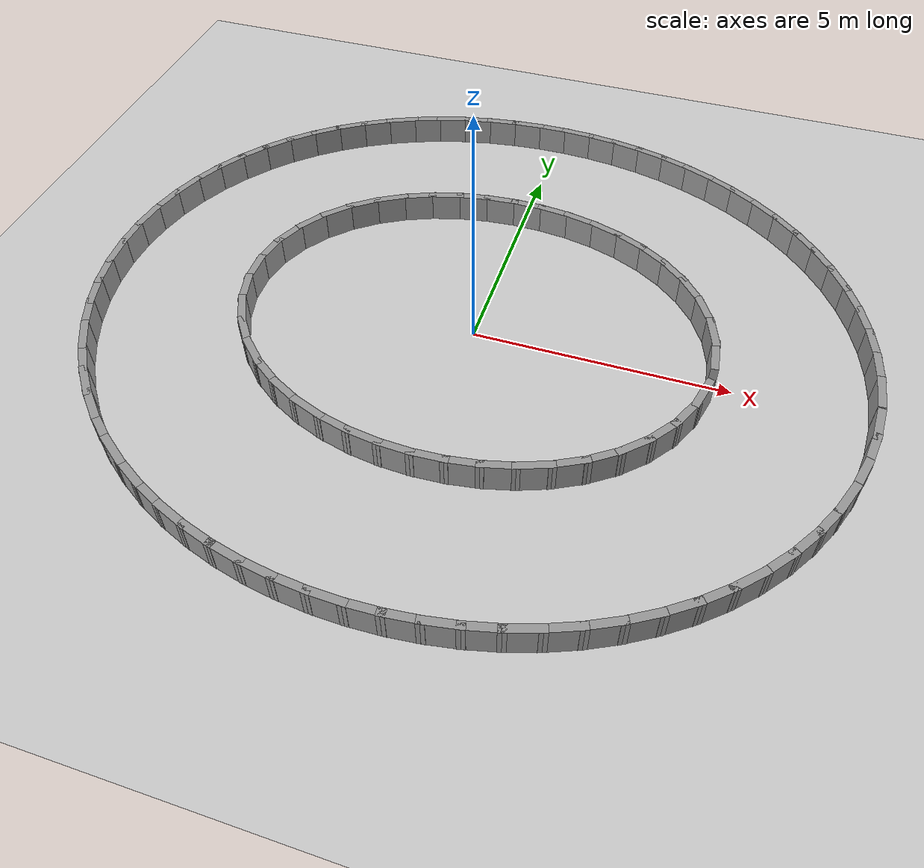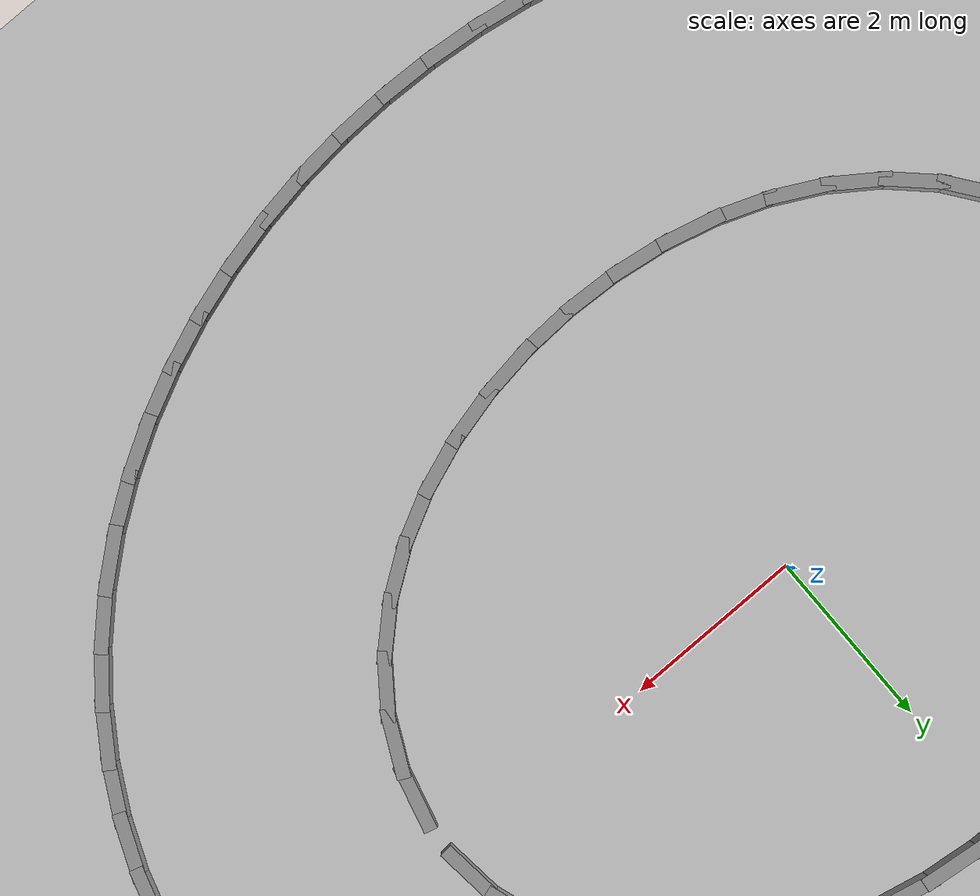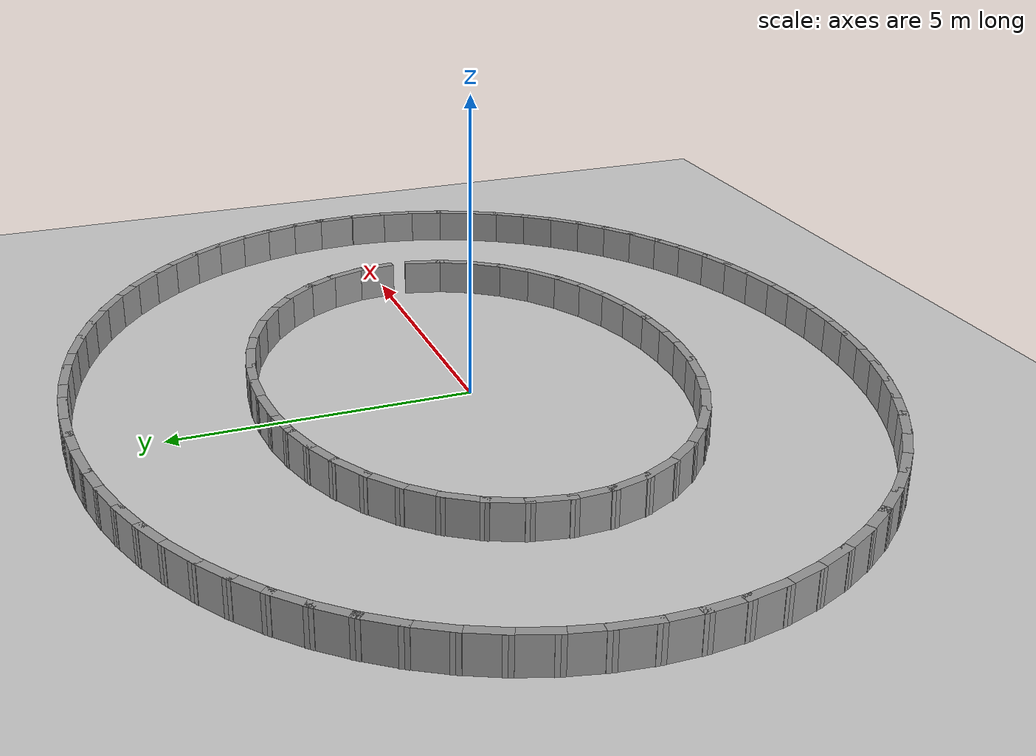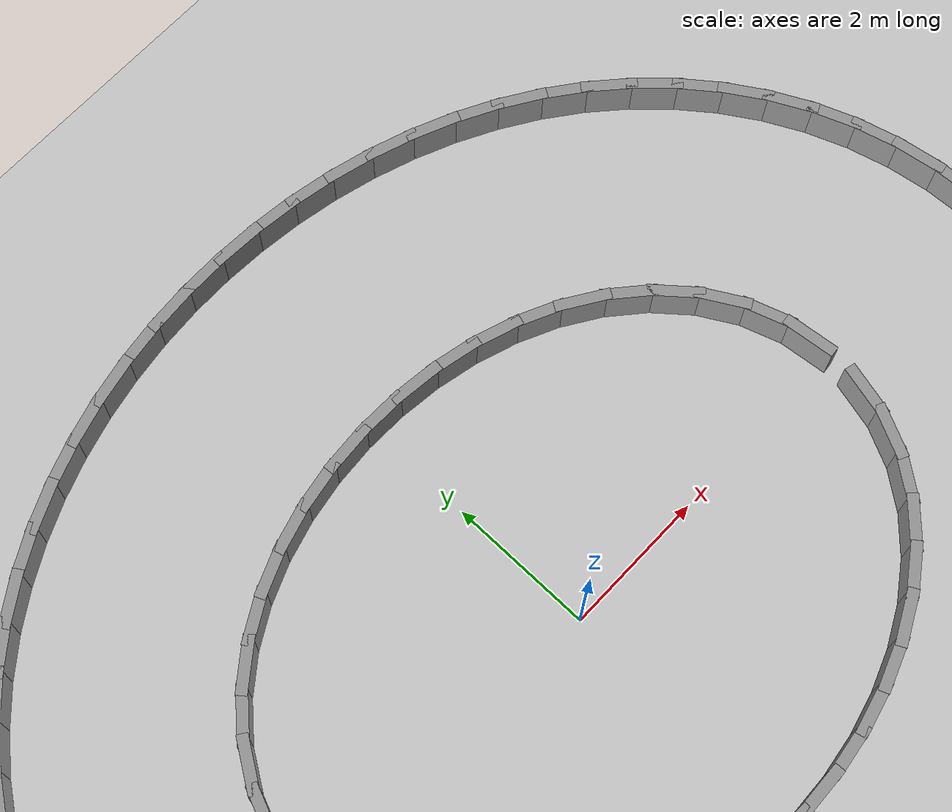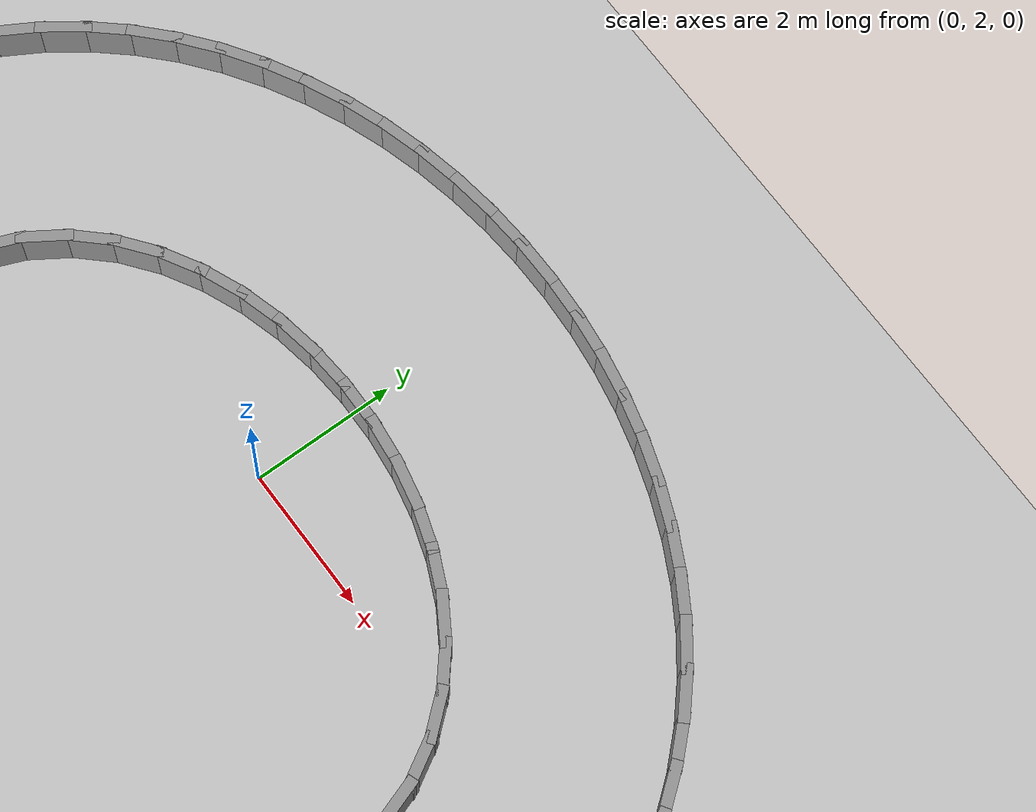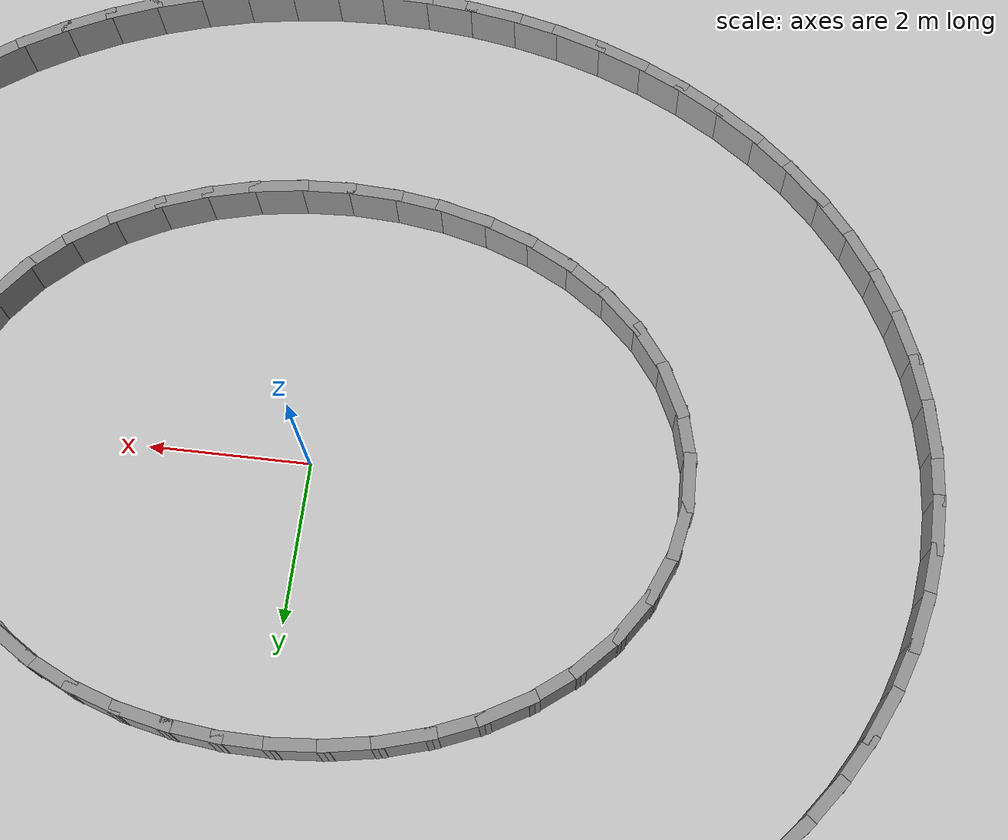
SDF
<?xml version="1.0" ?>
<sdf version='1.7'>
  <world name='default'>
    <plugin name='gazebo_ros_state' filename='libgazebo_ros_state.so'>
      <ros>
        <namespace>/</namespace>
      </ros>
      <update_rate>1000.0</update_rate>
    </plugin>

    <light name='sun' type='directional'>
      <cast_shadows>1</cast_shadows>
      <pose>0 0 10 0 -0 0</pose>
      <diffuse>0.8 0.8 0.8 1</diffuse>
      <specular>0.2 0.2 0.2 1</specular>
      <attenuation>
        <range>1000</range>
        <constant>0.9</constant>
        <linear>0.01</linear>
        <quadratic>0.001</quadratic>
      </attenuation>
      <direction>-0.5 0.1 -0.9</direction>
      <spot>
        <inner_angle>0</inner_angle>
        <outer_angle>0</outer_angle>
        <falloff>0</falloff>
      </spot>
    </light>
    <model name='ground_plane'>
      <static>1</static>
      <link name='link'>
        <collision name='collision'>
          <geometry>
            <plane>
              <normal>0 0 1</normal>
              <size>100 100</size>
            </plane>
          </geometry>
          <surface>
            <friction>
              <ode>
                <mu>100</mu>
                <mu2>50</mu2>
              </ode>
              <torsional>
                <ode/>
              </torsional>
            </friction>
            <contact>
              <ode/>
            </contact>
            <bounce/>
          </surface>
          <max_contacts>10</max_contacts>
        </collision>
        <visual name='visual'>
          <cast_shadows>0</cast_shadows>
          <geometry>
            <plane>
              <normal>0 0 1</normal>
              <size>100 100</size>
            </plane>
          </geometry>
          <material>
            <script>
              <uri>file://media/materials/scripts/gazebo.material</uri>
              <name>Gazebo/Grey</name>
            </script>
          </material>
        </visual>
        <self_collide>0</self_collide>
        <enable_wind>0</enable_wind>
        <kinematic>0</kinematic>
      </link>
    </model>
    <gravity>0 0 -9.8</gravity>
    <magnetic_field>6e-06 2.3e-05 -4.2e-05</magnetic_field>
    <atmosphere type='adiabatic'/>
    <physics type='ode'>
      <max_step_size>0.001</max_step_size>
      <real_time_factor>1</real_time_factor>
      <real_time_update_rate>1000</real_time_update_rate>
    </physics>
    <scene>
      <ambient>0.4 0.4 0.4 1</ambient>
      <background>0.7 0.7 0.7 1</background>
      <shadows>1</shadows>
    </scene>
    <audio>
      <device>default</device>
    </audio>
    <wind/>
    <spherical_coordinates>
      <surface_model>EARTH_WGS84</surface_model>
      <latitude_deg>0</latitude_deg>
      <longitude_deg>0</longitude_deg>
      <elevation>0</elevation>
      <heading_deg>0</heading_deg>
    </spherical_coordinates>
  <model name='rand_lobed_00'>
    <pose>0 0 0 0 -0 0</pose>
    <link name='Wall_0'>
      <collision name='Wall_0_Collision'>
        <geometry><box><size>0.7488 0.1500 0.6000</size></box></geometry>
        <pose>0 0 0.3000 0 -0 0</pose>
      </collision>
      <visual name='Wall_0_Visual'>
        <pose>0 0 0.3000 0 -0 0</pose>
        <geometry><box><size>0.7488 0.1500 0.6000</size></box></geometry>
        <material>
          <script>
            <uri>file://media/materials/scripts/gazebo.material</uri>
            <name>Gazebo/Grey</name>
          </script>
          <ambient>1 1 1 1</ambient>
        </material>
      </visual>
      <pose>4.5601 0.2977 0 0 -0 1.67916</pose>
    </link>
    <link name='Wall_1'>
      <collision name='Wall_1_Collision'>
        <geometry><box><size>0.7489 0.1500 0.6000</size></box></geometry>
        <pose>0 0 0.3000 0 -0 0</pose>
      </collision>
      <visual name='Wall_1_Visual'>
        <pose>0 0 0.3000 0 -0 0</pose>
        <geometry><box><size>0.7489 0.1500 0.6000</size></box></geometry>
        <material>
          <script>
            <uri>file://media/materials/scripts/gazebo.material</uri>
            <name>Gazebo/Grey</name>
          </script>
          <ambient>1 1 1 1</ambient>
        </material>
      </visual>
      <pose>4.4335 0.8796 0 0 -0 1.89073</pose>
    </link>
    <link name='Wall_2'>
      <collision name='Wall_2_Collision'>
        <geometry><box><size>0.7491 0.1500 0.6000</size></box></geometry>
        <pose>0 0 0.3000 0 -0 0</pose>
      </collision>
      <visual name='Wall_2_Visual'>
        <pose>0 0 0.3000 0 -0 0</pose>
        <geometry><box><size>0.7491 0.1500 0.6000</size></box></geometry>
        <material>
          <script>
            <uri>file://media/materials/scripts/gazebo.material</uri>
            <name>Gazebo/Grey</name>
          </script>
          <ambient>1 1 1 1</ambient>
        </material>
      </visual>
      <pose>4.1910 1.4241 0 0 -0 2.08895</pose>
    </link>
    <link name='Wall_3'>
      <collision name='Wall_3_Collision'>
        <geometry><box><size>0.7493 0.1500 0.6000</size></box></geometry>
        <pose>0 0 0.3000 0 -0 0</pose>
      </collision>
      <visual name='Wall_3_Visual'>
        <pose>0 0 0.3000 0 -0 0</pose>
        <geometry><box><size>0.7493 0.1500 0.6000</size></box></geometry>
        <material>
          <script>
            <uri>file://media/materials/scripts/gazebo.material</uri>
            <name>Gazebo/Grey</name>
          </script>
          <ambient>1 1 1 1</ambient>
        </material>
      </visual>
      <pose>3.8499 1.9137 0 0 -0 2.26951</pose>
    </link>
    <link name='Wall_4'>
      <collision name='Wall_4_Collision'>
        <geometry><box><size>0.7494 0.1500 0.6000</size></box></geometry>
        <pose>0 0 0.3000 0 -0 0</pose>
      </collision>
      <visual name='Wall_4_Visual'>
        <pose>0 0 0.3000 0 -0 0</pose>
        <geometry><box><size>0.7494 0.1500 0.6000</size></box></geometry>
        <material>
          <script>
            <uri>file://media/materials/scripts/gazebo.material</uri>
            <name>Gazebo/Grey</name>
          </script>
          <ambient>1 1 1 1</ambient>
        </material>
      </visual>
      <pose>3.4299 2.3385 0 0 -0 2.43161</pose>
    </link>
    <link name='Wall_5'>
      <collision name='Wall_5_Collision'>
        <geometry><box><size>0.7495 0.1500 0.6000</size></box></geometry>
        <pose>0 0 0.3000 0 -0 0</pose>
      </collision>
      <visual name='Wall_5_Visual'>
        <pose>0 0 0.3000 0 -0 0</pose>
        <geometry><box><size>0.7495 0.1500 0.6000</size></box></geometry>
        <material>
          <script>
            <uri>file://media/materials/scripts/gazebo.material</uri>
            <name>Gazebo/Grey</name>
          </script>
          <ambient>1 1 1 1</ambient>
        </material>
      </visual>
      <pose>2.9494 2.6944 0 0 -0 2.57654</pose>
    </link>
    <link name='Wall_6'>
      <collision name='Wall_6_Collision'>
        <geometry><box><size>0.7496 0.1500 0.6000</size></box></geometry>
        <pose>0 0 0.3000 0 -0 0</pose>
      </collision>
      <visual name='Wall_6_Visual'>
        <pose>0 0 0.3000 0 -0 0</pose>
        <geometry><box><size>0.7496 0.1500 0.6000</size></box></geometry>
        <material>
          <script>
            <uri>file://media/materials/scripts/gazebo.material</uri>
            <name>Gazebo/Grey</name>
          </script>
          <ambient>1 1 1 1</ambient>
        </material>
      </visual>
      <pose>2.4244 2.9813 0 0 -0 2.70636</pose>
    </link>
    <link name='Wall_7'>
      <collision name='Wall_7_Collision'>
        <geometry><box><size>0.7497 0.1500 0.6000</size></box></geometry>
        <pose>0 0 0.3000 0 -0 0</pose>
      </collision>
      <visual name='Wall_7_Visual'>
        <pose>0 0 0.3000 0 -0 0</pose>
        <geometry><box><size>0.7497 0.1500 0.6000</size></box></geometry>
        <material>
          <script>
            <uri>file://media/materials/scripts/gazebo.material</uri>
            <name>Gazebo/Grey</name>
          </script>
          <ambient>1 1 1 1</ambient>
        </material>
      </visual>
      <pose>1.8677 3.2015 0 0 -0 2.82345</pose>
    </link>
    <link name='Wall_8'>
      <collision name='Wall_8_Collision'>
        <geometry><box><size>0.7497 0.1500 0.6000</size></box></geometry>
        <pose>0 0 0.3000 0 -0 0</pose>
      </collision>
      <visual name='Wall_8_Visual'>
        <pose>0 0 0.3000 0 -0 0</pose>
        <geometry><box><size>0.7497 0.1500 0.6000</size></box></geometry>
        <material>
          <script>
            <uri>file://media/materials/scripts/gazebo.material</uri>
            <name>Gazebo/Grey</name>
          </script>
          <ambient>1 1 1 1</ambient>
        </material>
      </visual>
      <pose>1.2897 3.3581 0 0 -0 2.93041</pose>
    </link>
    <link name='Wall_9'>
      <collision name='Wall_9_Collision'>
        <geometry><box><size>0.7498 0.1500 0.6000</size></box></geometry>
        <pose>0 0 0.3000 0 -0 0</pose>
      </collision>
      <visual name='Wall_9_Visual'>
        <pose>0 0 0.3000 0 -0 0</pose>
        <geometry><box><size>0.7498 0.1500 0.6000</size></box></geometry>
        <material>
          <script>
            <uri>file://media/materials/scripts/gazebo.material</uri>
            <name>Gazebo/Grey</name>
          </script>
          <ambient>1 1 1 1</ambient>
        </material>
      </visual>
      <pose>0.6985 3.4544 0 0 -0 3.03008</pose>
    </link>
    <link name='Wall_10'>
      <collision name='Wall_10_Collision'>
        <geometry><box><size>0.7498 0.1500 0.6000</size></box></geometry>
        <pose>0 0 0.3000 0 -0 0</pose>
      </collision>
      <visual name='Wall_10_Visual'>
        <pose>0 0 0.3000 0 -0 0</pose>
        <geometry><box><size>0.7498 0.1500 0.6000</size></box></geometry>
        <material>
          <script>
            <uri>file://media/materials/scripts/gazebo.material</uri>
            <name>Gazebo/Grey</name>
          </script>
          <ambient>1 1 1 1</ambient>
        </material>
      </visual>
      <pose>0.1006 3.4925 0 0 -0 3.12569</pose>
    </link>
    <link name='Wall_11'>
      <collision name='Wall_11_Collision'>
        <geometry><box><size>0.7498 0.1500 0.6000</size></box></geometry>
        <pose>0 0 0.3000 0 -0 0</pose>
      </collision>
      <visual name='Wall_11_Visual'>
        <pose>0 0 0.3000 0 -0 0</pose>
        <geometry><box><size>0.7498 0.1500 0.6000</size></box></geometry>
        <material>
          <script>
            <uri>file://media/materials/scripts/gazebo.material</uri>
            <name>Gazebo/Grey</name>
          </script>
          <ambient>1 1 1 1</ambient>
        </material>
      </visual>
      <pose>-0.4982 3.4736 0 0 -0 -3.06247</pose>
    </link>
    <link name='Wall_12'>
      <collision name='Wall_12_Collision'>
        <geometry><box><size>0.7497 0.1500 0.6000</size></box></geometry>
        <pose>0 0 0.3000 0 -0 0</pose>
      </collision>
      <visual name='Wall_12_Visual'>
        <pose>0 0 0.3000 0 -0 0</pose>
        <geometry><box><size>0.7497 0.1500 0.6000</size></box></geometry>
        <material>
          <script>
            <uri>file://media/materials/scripts/gazebo.material</uri>
            <name>Gazebo/Grey</name>
          </script>
          <ambient>1 1 1 1</ambient>
        </material>
      </visual>
      <pose>-1.0923 3.3971 0 0 -0 -2.96452</pose>
    </link>
    <link name='Wall_13'>
      <collision name='Wall_13_Collision'>
        <geometry><box><size>0.7497 0.1500 0.6000</size></box></geometry>
        <pose>0 0 0.3000 0 -0 0</pose>
      </collision>
      <visual name='Wall_13_Visual'>
        <pose>0 0 0.3000 0 -0 0</pose>
        <geometry><box><size>0.7497 0.1500 0.6000</size></box></geometry>
        <material>
          <script>
            <uri>file://media/materials/scripts/gazebo.material</uri>
            <name>Gazebo/Grey</name>
          </script>
          <ambient>1 1 1 1</ambient>
        </material>
      </visual>
      <pose>-1.6756 3.2610 0 0 -0 -2.86036</pose>
    </link>
    <link name='Wall_14'>
      <collision name='Wall_14_Collision'>
        <geometry><box><size>0.7496 0.1500 0.6000</size></box></geometry>
        <pose>0 0 0.3000 0 -0 0</pose>
      </collision>
      <visual name='Wall_14_Visual'>
        <pose>0 0 0.3000 0 -0 0</pose>
        <geometry><box><size>0.7496 0.1500 0.6000</size></box></geometry>
        <material>
          <script>
            <uri>file://media/materials/scripts/gazebo.material</uri>
            <name>Gazebo/Grey</name>
          </script>
          <ambient>1 1 1 1</ambient>
        </material>
      </visual>
      <pose>-2.2404 3.0625 0 0 -0 -2.74700</pose>
    </link>
    <link name='Wall_15'>
      <collision name='Wall_15_Collision'>
        <geometry><box><size>0.7496 0.1500 0.6000</size></box></geometry>
        <pose>0 0 0.3000 0 -0 0</pose>
      </collision>
      <visual name='Wall_15_Visual'>
        <pose>0 0 0.3000 0 -0 0</pose>
        <geometry><box><size>0.7496 0.1500 0.6000</size></box></geometry>
        <material>
          <script>
            <uri>file://media/materials/scripts/gazebo.material</uri>
            <name>Gazebo/Grey</name>
          </script>
          <ambient>1 1 1 1</ambient>
        </material>
      </visual>
      <pose>-2.7774 2.7983 0 0 -0 -2.62170</pose>
    </link>
    <link name='Wall_16'>
      <collision name='Wall_16_Collision'>
        <geometry><box><size>0.7495 0.1500 0.6000</size></box></geometry>
        <pose>0 0 0.3000 0 -0 0</pose>
      </collision>
      <visual name='Wall_16_Visual'>
        <pose>0 0 0.3000 0 -0 0</pose>
        <geometry><box><size>0.7495 0.1500 0.6000</size></box></geometry>
        <material>
          <script>
            <uri>file://media/materials/scripts/gazebo.material</uri>
            <name>Gazebo/Grey</name>
          </script>
          <ambient>1 1 1 1</ambient>
        </material>
      </visual>
      <pose>-3.2744 2.4658 0 0 -0 -2.48210</pose>
    </link>
    <link name='Wall_17'>
      <collision name='Wall_17_Collision'>
        <geometry><box><size>0.7493 0.1500 0.6000</size></box></geometry>
        <pose>0 0 0.3000 0 -0 0</pose>
      </collision>
      <visual name='Wall_17_Visual'>
        <pose>0 0 0.3000 0 -0 0</pose>
        <geometry><box><size>0.7493 0.1500 0.6000</size></box></geometry>
        <material>
          <script>
            <uri>file://media/materials/scripts/gazebo.material</uri>
            <name>Gazebo/Grey</name>
          </script>
          <ambient>1 1 1 1</ambient>
        </material>
      </visual>
      <pose>-3.7167 2.0639 0 0 -0 -2.32595</pose>
    </link>
    <link name='Wall_18'>
      <collision name='Wall_18_Collision'>
        <geometry><box><size>0.7492 0.1500 0.6000</size></box></geometry>
        <pose>0 0 0.3000 0 -0 0</pose>
      </collision>
      <visual name='Wall_18_Visual'>
        <pose>0 0 0.3000 0 -0 0</pose>
        <geometry><box><size>0.7492 0.1500 0.6000</size></box></geometry>
        <material>
          <script>
            <uri>file://media/materials/scripts/gazebo.material</uri>
            <name>Gazebo/Grey</name>
          </script>
          <ambient>1 1 1 1</ambient>
        </material>
      </visual>
      <pose>-4.0865 1.5953 0 0 -0 -2.15167</pose>
    </link>
    <link name='Wall_19'>
      <collision name='Wall_19_Collision'>
        <geometry><box><size>0.7490 0.1500 0.6000</size></box></geometry>
        <pose>0 0 0.3000 0 -0 0</pose>
      </collision>
      <visual name='Wall_19_Visual'>
        <pose>0 0 0.3000 0 -0 0</pose>
        <geometry><box><size>0.7490 0.1500 0.6000</size></box></geometry>
        <material>
          <script>
            <uri>file://media/materials/scripts/gazebo.material</uri>
            <name>Gazebo/Grey</name>
          </script>
          <ambient>1 1 1 1</ambient>
        </material>
      </visual>
      <pose>-4.3643 1.0676 0 0 -0 -1.95907</pose>
    </link>
    <link name='Wall_20'>
      <collision name='Wall_20_Collision'>
        <geometry><box><size>0.7489 0.1500 0.6000</size></box></geometry>
        <pose>0 0 0.3000 0 -0 0</pose>
      </collision>
      <visual name='Wall_20_Visual'>
        <pose>0 0 0.3000 0 -0 0</pose>
        <geometry><box><size>0.7489 0.1500 0.6000</size></box></geometry>
        <material>
          <script>
            <uri>file://media/materials/scripts/gazebo.material</uri>
            <name>Gazebo/Grey</name>
          </script>
          <ambient>1 1 1 1</ambient>
        </material>
      </visual>
      <pose>-4.5314 0.4959 0 0 -0 -1.75125</pose>
    </link>
    <link name='Wall_21'>
      <collision name='Wall_21_Collision'>
        <geometry><box><size>0.7488 0.1500 0.6000</size></box></geometry>
        <pose>0 0 0.3000 0 -0 0</pose>
      </collision>
      <visual name='Wall_21_Visual'>
        <pose>0 0 0.3000 0 -0 0</pose>
        <geometry><box><size>0.7488 0.1500 0.6000</size></box></geometry>
        <material>
          <script>
            <uri>file://media/materials/scripts/gazebo.material</uri>
            <name>Gazebo/Grey</name>
          </script>
          <ambient>1 1 1 1</ambient>
        </material>
      </visual>
      <pose>-4.5744 -0.0979 0 0 -0 -1.53515</pose>
    </link>
    <link name='Wall_22'>
      <collision name='Wall_22_Collision'>
        <geometry><box><size>0.7489 0.1500 0.6000</size></box></geometry>
        <pose>0 0 0.3000 0 -0 0</pose>
      </collision>
      <visual name='Wall_22_Visual'>
        <pose>0 0 0.3000 0 -0 0</pose>
        <geometry><box><size>0.7489 0.1500 0.6000</size></box></geometry>
        <material>
          <script>
            <uri>file://media/materials/scripts/gazebo.material</uri>
            <name>Gazebo/Grey</name>
          </script>
          <ambient>1 1 1 1</ambient>
        </material>
      </visual>
      <pose>-4.4897 -0.6873 0 0 -0 -1.32075</pose>
    </link>
    <link name='Wall_23'>
      <collision name='Wall_23_Collision'>
        <geometry><box><size>0.7490 0.1500 0.6000</size></box></geometry>
        <pose>0 0 0.3000 0 -0 0</pose>
      </collision>
      <visual name='Wall_23_Visual'>
        <pose>0 0 0.3000 0 -0 0</pose>
        <geometry><box><size>0.7490 0.1500 0.6000</size></box></geometry>
        <material>
          <script>
            <uri>file://media/materials/scripts/gazebo.material</uri>
            <name>Gazebo/Grey</name>
          </script>
          <ambient>1 1 1 1</ambient>
        </material>
      </visual>
      <pose>-4.2844 -1.2467 0 0 -0 -1.11735</pose>
    </link>
    <link name='Wall_24'>
      <collision name='Wall_24_Collision'>
        <geometry><box><size>0.7492 0.1500 0.6000</size></box></geometry>
        <pose>0 0 0.3000 0 -0 0</pose>
      </collision>
      <visual name='Wall_24_Visual'>
        <pose>0 0 0.3000 0 -0 0</pose>
        <geometry><box><size>0.7492 0.1500 0.6000</size></box></geometry>
        <material>
          <script>
            <uri>file://media/materials/scripts/gazebo.material</uri>
            <name>Gazebo/Grey</name>
          </script>
          <ambient>1 1 1 1</ambient>
        </material>
      </visual>
      <pose>-3.9742 -1.7562 0 0 -0 -0.93064</pose>
    </link>
    <link name='Wall_25'>
      <collision name='Wall_25_Collision'>
        <geometry><box><size>0.7494 0.1500 0.6000</size></box></geometry>
        <pose>0 0 0.3000 0 -0 0</pose>
      </collision>
      <visual name='Wall_25_Visual'>
        <pose>0 0 0.3000 0 -0 0</pose>
        <geometry><box><size>0.7494 0.1500 0.6000</size></box></geometry>
        <material>
          <script>
            <uri>file://media/materials/scripts/gazebo.material</uri>
            <name>Gazebo/Grey</name>
          </script>
          <ambient>1 1 1 1</ambient>
        </material>
      </visual>
      <pose>-3.5785 -2.2035 0 0 -0 -0.76241</pose>
    </link>
    <link name='Wall_26'>
      <collision name='Wall_26_Collision'>
        <geometry><box><size>0.7495 0.1500 0.6000</size></box></geometry>
        <pose>0 0 0.3000 0 -0 0</pose>
      </collision>
      <visual name='Wall_26_Visual'>
        <pose>0 0 0.3000 0 -0 0</pose>
        <geometry><box><size>0.7495 0.1500 0.6000</size></box></geometry>
        <material>
          <script>
            <uri>file://media/materials/scripts/gazebo.material</uri>
            <name>Gazebo/Grey</name>
          </script>
          <ambient>1 1 1 1</ambient>
        </material>
      </visual>
      <pose>-3.1164 -2.5826 0 0 -0 -0.61192</pose>
    </link>
    <link name='Wall_27'>
      <collision name='Wall_27_Collision'>
        <geometry><box><size>0.7496 0.1500 0.6000</size></box></geometry>
        <pose>0 0 0.3000 0 -0 0</pose>
      </collision>
      <visual name='Wall_27_Visual'>
        <pose>0 0 0.3000 0 -0 0</pose>
        <geometry><box><size>0.7496 0.1500 0.6000</size></box></geometry>
        <material>
          <script>
            <uri>file://media/materials/scripts/gazebo.material</uri>
            <name>Gazebo/Grey</name>
          </script>
          <ambient>1 1 1 1</ambient>
        </material>
      </visual>
      <pose>-2.6048 -2.8925 0 0 -0 -0.47728</pose>
    </link>
    <link name='Wall_28'>
      <collision name='Wall_28_Collision'>
        <geometry><box><size>0.7497 0.1500 0.6000</size></box></geometry>
        <pose>0 0 0.3000 0 -0 0</pose>
      </collision>
      <visual name='Wall_28_Visual'>
        <pose>0 0 0.3000 0 -0 0</pose>
        <geometry><box><size>0.7497 0.1500 0.6000</size></box></geometry>
        <material>
          <script>
            <uri>file://media/materials/scripts/gazebo.material</uri>
            <name>Gazebo/Grey</name>
          </script>
          <ambient>1 1 1 1</ambient>
        </material>
      </visual>
      <pose>-2.0575 -3.1348 0 0 -0 -0.35619</pose>
    </link>
    <link name='Wall_29'>
      <collision name='Wall_29_Collision'>
        <geometry><box><size>0.7497 0.1500 0.6000</size></box></geometry>
        <pose>0 0 0.3000 0 -0 0</pose>
      </collision>
      <visual name='Wall_29_Visual'>
        <pose>0 0 0.3000 0 -0 0</pose>
        <geometry><box><size>0.7497 0.1500 0.6000</size></box></geometry>
        <material>
          <script>
            <uri>file://media/materials/scripts/gazebo.material</uri>
            <name>Gazebo/Grey</name>
          </script>
          <ambient>1 1 1 1</ambient>
        </material>
      </visual>
      <pose>-1.4856 -3.3124 0 0 -0 -0.24614</pose>
    </link>
    <link name='Wall_30'>
      <collision name='Wall_30_Collision'>
        <geometry><box><size>0.7498 0.1500 0.6000</size></box></geometry>
        <pose>0 0 0.3000 0 -0 0</pose>
      </collision>
      <visual name='Wall_30_Visual'>
        <pose>0 0 0.3000 0 -0 0</pose>
        <geometry><box><size>0.7498 0.1500 0.6000</size></box></geometry>
        <material>
          <script>
            <uri>file://media/materials/scripts/gazebo.material</uri>
            <name>Gazebo/Grey</name>
          </script>
          <ambient>1 1 1 1</ambient>
        </material>
      </visual>
      <pose>-0.8981 -3.4286 0 0 -0 -0.14437</pose>
    </link>
    <link name='Wall_31'>
      <collision name='Wall_31_Collision'>
        <geometry><box><size>0.7498 0.1500 0.6000</size></box></geometry>
        <pose>0 0 0.3000 0 -0 0</pose>
      </collision>
      <visual name='Wall_31_Visual'>
        <pose>0 0 0.3000 0 -0 0</pose>
        <geometry><box><size>0.7498 0.1500 0.6000</size></box></geometry>
        <material>
          <script>
            <uri>file://media/materials/scripts/gazebo.material</uri>
            <name>Gazebo/Grey</name>
          </script>
          <ambient>1 1 1 1</ambient>
        </material>
      </visual>
      <pose>-0.3018 -3.4861 0 0 -0 -0.04777</pose>
    </link>
    <link name='Wall_32'>
      <collision name='Wall_32_Collision'>
        <geometry><box><size>0.7498 0.1500 0.6000</size></box></geometry>
        <pose>0 0 0.3000 0 -0 0</pose>
      </collision>
      <visual name='Wall_32_Visual'>
        <pose>0 0 0.3000 0 -0 0</pose>
        <geometry><box><size>0.7498 0.1500 0.6000</size></box></geometry>
        <material>
          <script>
            <uri>file://media/materials/scripts/gazebo.material</uri>
            <name>Gazebo/Grey</name>
          </script>
          <ambient>1 1 1 1</ambient>
        </material>
      </visual>
      <pose>0.2973 -3.4863 0 0 -0 0.04707</pose>
    </link>
    <link name='Wall_33'>
      <collision name='Wall_33_Collision'>
        <geometry><box><size>0.7498 0.1500 0.6000</size></box></geometry>
        <pose>0 0 0.3000 0 -0 0</pose>
      </collision>
      <visual name='Wall_33_Visual'>
        <pose>0 0 0.3000 0 -0 0</pose>
        <geometry><box><size>0.7498 0.1500 0.6000</size></box></geometry>
        <material>
          <script>
            <uri>file://media/materials/scripts/gazebo.material</uri>
            <name>Gazebo/Grey</name>
          </script>
          <ambient>1 1 1 1</ambient>
        </material>
      </visual>
      <pose>0.8937 -3.4293 0 0 -0 0.14364</pose>
    </link>
    <link name='Wall_34'>
      <collision name='Wall_34_Collision'>
        <geometry><box><size>0.7497 0.1500 0.6000</size></box></geometry>
        <pose>0 0 0.3000 0 -0 0</pose>
      </collision>
      <visual name='Wall_34_Visual'>
        <pose>0 0 0.3000 0 -0 0</pose>
        <geometry><box><size>0.7497 0.1500 0.6000</size></box></geometry>
        <material>
          <script>
            <uri>file://media/materials/scripts/gazebo.material</uri>
            <name>Gazebo/Grey</name>
          </script>
          <ambient>1 1 1 1</ambient>
        </material>
      </visual>
      <pose>1.4814 -3.3135 0 0 -0 0.24536</pose>
    </link>
    <link name='Wall_35'>
      <collision name='Wall_35_Collision'>
        <geometry><box><size>0.7497 0.1500 0.6000</size></box></geometry>
        <pose>0 0 0.3000 0 -0 0</pose>
      </collision>
      <visual name='Wall_35_Visual'>
        <pose>0 0 0.3000 0 -0 0</pose>
        <geometry><box><size>0.7497 0.1500 0.6000</size></box></geometry>
        <material>
          <script>
            <uri>file://media/materials/scripts/gazebo.material</uri>
            <name>Gazebo/Grey</name>
          </script>
          <ambient>1 1 1 1</ambient>
        </material>
      </visual>
      <pose>2.0533 -3.1364 0 0 -0 0.35534</pose>
    </link>
    <link name='Wall_36'>
      <collision name='Wall_36_Collision'>
        <geometry><box><size>0.7496 0.1500 0.6000</size></box></geometry>
        <pose>0 0 0.3000 0 -0 0</pose>
      </collision>
      <visual name='Wall_36_Visual'>
        <pose>0 0 0.3000 0 -0 0</pose>
        <geometry><box><size>0.7496 0.1500 0.6000</size></box></geometry>
        <material>
          <script>
            <uri>file://media/materials/scripts/gazebo.material</uri>
            <name>Gazebo/Grey</name>
          </script>
          <ambient>1 1 1 1</ambient>
        </material>
      </visual>
      <pose>2.6009 -2.8946 0 0 -0 0.47632</pose>
    </link>
    <link name='Wall_37'>
      <collision name='Wall_37_Collision'>
        <geometry><box><size>0.7495 0.1500 0.6000</size></box></geometry>
        <pose>0 0 0.3000 0 -0 0</pose>
      </collision>
      <visual name='Wall_37_Visual'>
        <pose>0 0 0.3000 0 -0 0</pose>
        <geometry><box><size>0.7495 0.1500 0.6000</size></box></geometry>
        <material>
          <script>
            <uri>file://media/materials/scripts/gazebo.material</uri>
            <name>Gazebo/Grey</name>
          </script>
          <ambient>1 1 1 1</ambient>
        </material>
      </visual>
      <pose>3.1128 -2.5852 0 0 -0 0.61088</pose>
    </link>
    <link name='Wall_38'>
      <collision name='Wall_38_Collision'>
        <geometry><box><size>0.7494 0.1500 0.6000</size></box></geometry>
        <pose>0 0 0.3000 0 -0 0</pose>
      </collision>
      <visual name='Wall_38_Visual'>
        <pose>0 0 0.3000 0 -0 0</pose>
        <geometry><box><size>0.7494 0.1500 0.6000</size></box></geometry>
        <material>
          <script>
            <uri>file://media/materials/scripts/gazebo.material</uri>
            <name>Gazebo/Grey</name>
          </script>
          <ambient>1 1 1 1</ambient>
        </material>
      </visual>
      <pose>3.5753 -2.2065 0 0 -0 0.76124</pose>
    </link>
    <link name='Wall_39'>
      <collision name='Wall_39_Collision'>
        <geometry><box><size>0.7492 0.1500 0.6000</size></box></geometry>
        <pose>0 0 0.3000 0 -0 0</pose>
      </collision>
      <visual name='Wall_39_Visual'>
        <pose>0 0 0.3000 0 -0 0</pose>
        <geometry><box><size>0.7492 0.1500 0.6000</size></box></geometry>
        <material>
          <script>
            <uri>file://media/materials/scripts/gazebo.material</uri>
            <name>Gazebo/Grey</name>
          </script>
          <ambient>1 1 1 1</ambient>
        </material>
      </visual>
      <pose>3.9716 -1.7597 0 0 -0 0.92933</pose>
    </link>
    <link name='Wall_40'>
      <collision name='Wall_40_Collision'>
        <geometry><box><size>0.7490 0.1500 0.6000</size></box></geometry>
        <pose>0 0 0.3000 0 -0 0</pose>
      </collision>
      <visual name='Wall_40_Visual'>
        <pose>0 0 0.3000 0 -0 0</pose>
        <geometry><box><size>0.7490 0.1500 0.6000</size></box></geometry>
        <material>
          <script>
            <uri>file://media/materials/scripts/gazebo.material</uri>
            <name>Gazebo/Grey</name>
          </script>
          <ambient>1 1 1 1</ambient>
        </material>
      </visual>
      <pose>4.2824 -1.2506 0 0 -0 1.11591</pose>
    </link>
    <link name='Wall_41'>
      <collision name='Wall_41_Collision'>
        <geometry><box><size>0.7489 0.1500 0.6000</size></box></geometry>
        <pose>0 0 0.3000 0 -0 0</pose>
      </collision>
      <visual name='Wall_41_Visual'>
        <pose>0 0 0.3000 0 -0 0</pose>
        <geometry><box><size>0.7489 0.1500 0.6000</size></box></geometry>
        <material>
          <script>
            <uri>file://media/materials/scripts/gazebo.material</uri>
            <name>Gazebo/Grey</name>
          </script>
          <ambient>1 1 1 1</ambient>
        </material>
      </visual>
      <pose>4.4886 -0.6915 0 0 -0 1.31920</pose>
    </link>
    <link name='Wall_42'>
      <collision name='Wall_42_Collision'>
        <geometry><box><size>0.7497 0.1500 0.6000</size></box></geometry>
        <pose>0 0 0.3000 0 -0 0</pose>
      </collision>
      <visual name='Wall_42_Visual'>
        <pose>0 0 0.3000 0 -0 0</pose>
        <geometry><box><size>0.7497 0.1500 0.6000</size></box></geometry>
        <material>
          <script>
            <uri>file://media/materials/scripts/gazebo.material</uri>
            <name>Gazebo/Grey</name>
          </script>
          <ambient>1 1 1 1</ambient>
        </material>
      </visual>
      <pose>7.5006 0.2994 0 0 -0 1.62361</pose>
    </link>
    <link name='Wall_43'>
      <collision name='Wall_43_Collision'>
        <geometry><box><size>0.7497 0.1500 0.6000</size></box></geometry>
        <pose>0 0 0.3000 0 -0 0</pose>
      </collision>
      <visual name='Wall_43_Visual'>
        <pose>0 0 0.3000 0 -0 0</pose>
        <geometry><box><size>0.7497 0.1500 0.6000</size></box></geometry>
        <material>
          <script>
            <uri>file://media/materials/scripts/gazebo.material</uri>
            <name>Gazebo/Grey</name>
          </script>
          <ambient>1 1 1 1</ambient>
        </material>
      </visual>
      <pose>7.4376 0.8950 0 0 -0 1.72884</pose>
    </link>
    <link name='Wall_44'>
      <collision name='Wall_44_Collision'>
        <geometry><box><size>0.7497 0.1500 0.6000</size></box></geometry>
        <pose>0 0 0.3000 0 -0 0</pose>
      </collision>
      <visual name='Wall_44_Visual'>
        <pose>0 0 0.3000 0 -0 0</pose>
        <geometry><box><size>0.7497 0.1500 0.6000</size></box></geometry>
        <material>
          <script>
            <uri>file://media/materials/scripts/gazebo.material</uri>
            <name>Gazebo/Grey</name>
          </script>
          <ambient>1 1 1 1</ambient>
        </material>
      </visual>
      <pose>7.3126 1.4807 0 0 -0 1.83319</pose>
    </link>
    <link name='Wall_45'>
      <collision name='Wall_45_Collision'>
        <geometry><box><size>0.7497 0.1500 0.6000</size></box></geometry>
        <pose>0 0 0.3000 0 -0 0</pose>
      </collision>
      <visual name='Wall_45_Visual'>
        <pose>0 0 0.3000 0 -0 0</pose>
        <geometry><box><size>0.7497 0.1500 0.6000</size></box></geometry>
        <material>
          <script>
            <uri>file://media/materials/scripts/gazebo.material</uri>
            <name>Gazebo/Grey</name>
          </script>
          <ambient>1 1 1 1</ambient>
        </material>
      </visual>
      <pose>7.1277 2.0504 0 0 -0 1.93611</pose>
    </link>
    <link name='Wall_46'>
      <collision name='Wall_46_Collision'>
        <geometry><box><size>0.7497 0.1500 0.6000</size></box></geometry>
        <pose>0 0 0.3000 0 -0 0</pose>
      </collision>
      <visual name='Wall_46_Visual'>
        <pose>0 0 0.3000 0 -0 0</pose>
        <geometry><box><size>0.7497 0.1500 0.6000</size></box></geometry>
        <material>
          <script>
            <uri>file://media/materials/scripts/gazebo.material</uri>
            <name>Gazebo/Grey</name>
          </script>
          <ambient>1 1 1 1</ambient>
        </material>
      </visual>
      <pose>6.8857 2.5984 0 0 -0 2.03712</pose>
    </link>
    <link name='Wall_47'>
      <collision name='Wall_47_Collision'>
        <geometry><box><size>0.7498 0.1500 0.6000</size></box></geometry>
        <pose>0 0 0.3000 0 -0 0</pose>
      </collision>
      <visual name='Wall_47_Visual'>
        <pose>0 0 0.3000 0 -0 0</pose>
        <geometry><box><size>0.7498 0.1500 0.6000</size></box></geometry>
        <material>
          <script>
            <uri>file://media/materials/scripts/gazebo.material</uri>
            <name>Gazebo/Grey</name>
          </script>
          <ambient>1 1 1 1</ambient>
        </material>
      </visual>
      <pose>6.5904 3.1195 0 0 -0 2.13579</pose>
    </link>
    <link name='Wall_48'>
      <collision name='Wall_48_Collision'>
        <geometry><box><size>0.7498 0.1500 0.6000</size></box></geometry>
        <pose>0 0 0.3000 0 -0 0</pose>
      </collision>
      <visual name='Wall_48_Visual'>
        <pose>0 0 0.3000 0 -0 0</pose>
        <geometry><box><size>0.7498 0.1500 0.6000</size></box></geometry>
        <material>
          <script>
            <uri>file://media/materials/scripts/gazebo.material</uri>
            <name>Gazebo/Grey</name>
          </script>
          <ambient>1 1 1 1</ambient>
        </material>
      </visual>
      <pose>6.2457 3.6095 0 0 -0 2.23176</pose>
    </link>
    <link name='Wall_49'>
      <collision name='Wall_49_Collision'>
        <geometry><box><size>0.7498 0.1500 0.6000</size></box></geometry>
        <pose>0 0 0.3000 0 -0 0</pose>
      </collision>
      <visual name='Wall_49_Visual'>
        <pose>0 0 0.3000 0 -0 0</pose>
        <geometry><box><size>0.7498 0.1500 0.6000</size></box></geometry>
        <material>
          <script>
            <uri>file://media/materials/scripts/gazebo.material</uri>
            <name>Gazebo/Grey</name>
          </script>
          <ambient>1 1 1 1</ambient>
        </material>
      </visual>
      <pose>5.8563 4.0648 0 0 -0 2.32478</pose>
    </link>
    <link name='Wall_50'>
      <collision name='Wall_50_Collision'>
        <geometry><box><size>0.7498 0.1500 0.6000</size></box></geometry>
        <pose>0 0 0.3000 0 -0 0</pose>
      </collision>
      <visual name='Wall_50_Visual'>
        <pose>0 0 0.3000 0 -0 0</pose>
        <geometry><box><size>0.7498 0.1500 0.6000</size></box></geometry>
        <material>
          <script>
            <uri>file://media/materials/scripts/gazebo.material</uri>
            <name>Gazebo/Grey</name>
          </script>
          <ambient>1 1 1 1</ambient>
        </material>
      </visual>
      <pose>5.4269 4.4828 0 0 -0 2.41474</pose>
    </link>
    <link name='Wall_51'>
      <collision name='Wall_51_Collision'>
        <geometry><box><size>0.7498 0.1500 0.6000</size></box></geometry>
        <pose>0 0 0.3000 0 -0 0</pose>
      </collision>
      <visual name='Wall_51_Visual'>
        <pose>0 0 0.3000 0 -0 0</pose>
        <geometry><box><size>0.7498 0.1500 0.6000</size></box></geometry>
        <material>
          <script>
            <uri>file://media/materials/scripts/gazebo.material</uri>
            <name>Gazebo/Grey</name>
          </script>
          <ambient>1 1 1 1</ambient>
        </material>
      </visual>
      <pose>4.9623 4.8612 0 0 -0 2.50144</pose>
    </link>
    <link name='Wall_52'>
      <collision name='Wall_52_Collision'>
        <geometry><box><size>0.7498 0.1500 0.6000</size></box></geometry>
        <pose>0 0 0.3000 0 -0 0</pose>
      </collision>
      <visual name='Wall_52_Visual'>
        <pose>0 0 0.3000 0 -0 0</pose>
        <geometry><box><size>0.7498 0.1500 0.6000</size></box></geometry>
        <material>
          <script>
            <uri>file://media/materials/scripts/gazebo.material</uri>
            <name>Gazebo/Grey</name>
          </script>
          <ambient>1 1 1 1</ambient>
        </material>
      </visual>
      <pose>4.4671 5.1988 0 0 -0 2.58486</pose>
    </link>
    <link name='Wall_53'>
      <collision name='Wall_53_Collision'>
        <geometry><box><size>0.7498 0.1500 0.6000</size></box></geometry>
        <pose>0 0 0.3000 0 -0 0</pose>
      </collision>
      <visual name='Wall_53_Visual'>
        <pose>0 0 0.3000 0 -0 0</pose>
        <geometry><box><size>0.7498 0.1500 0.6000</size></box></geometry>
        <material>
          <script>
            <uri>file://media/materials/scripts/gazebo.material</uri>
            <name>Gazebo/Grey</name>
          </script>
          <ambient>1 1 1 1</ambient>
        </material>
      </visual>
      <pose>3.9460 5.4949 0 0 -0 2.66509</pose>
    </link>
    <link name='Wall_54'>
      <collision name='Wall_54_Collision'>
        <geometry><box><size>0.7499 0.1500 0.6000</size></box></geometry>
        <pose>0 0 0.3000 0 -0 0</pose>
      </collision>
      <visual name='Wall_54_Visual'>
        <pose>0 0 0.3000 0 -0 0</pose>
        <geometry><box><size>0.7499 0.1500 0.6000</size></box></geometry>
        <material>
          <script>
            <uri>file://media/materials/scripts/gazebo.material</uri>
            <name>Gazebo/Grey</name>
          </script>
          <ambient>1 1 1 1</ambient>
        </material>
      </visual>
      <pose>3.4032 5.7491 0 0 -0 2.74207</pose>
    </link>
    <link name='Wall_55'>
      <collision name='Wall_55_Collision'>
        <geometry><box><size>0.7499 0.1500 0.6000</size></box></geometry>
        <pose>0 0 0.3000 0 -0 0</pose>
      </collision>
      <visual name='Wall_55_Visual'>
        <pose>0 0 0.3000 0 -0 0</pose>
        <geometry><box><size>0.7499 0.1500 0.6000</size></box></geometry>
        <material>
          <script>
            <uri>file://media/materials/scripts/gazebo.material</uri>
            <name>Gazebo/Grey</name>
          </script>
          <ambient>1 1 1 1</ambient>
        </material>
      </visual>
      <pose>2.8427 5.9617 0 0 -0 2.81606</pose>
    </link>
    <link name='Wall_56'>
      <collision name='Wall_56_Collision'>
        <geometry><box><size>0.7499 0.1500 0.6000</size></box></geometry>
        <pose>0 0 0.3000 0 -0 0</pose>
      </collision>
      <visual name='Wall_56_Visual'>
        <pose>0 0 0.3000 0 -0 0</pose>
        <geometry><box><size>0.7499 0.1500 0.6000</size></box></geometry>
        <material>
          <script>
            <uri>file://media/materials/scripts/gazebo.material</uri>
            <name>Gazebo/Grey</name>
          </script>
          <ambient>1 1 1 1</ambient>
        </material>
      </visual>
      <pose>2.2682 6.1331 0 0 -0 2.88723</pose>
    </link>
    <link name='Wall_57'>
      <collision name='Wall_57_Collision'>
        <geometry><box><size>0.7499 0.1500 0.6000</size></box></geometry>
        <pose>0 0 0.3000 0 -0 0</pose>
      </collision>
      <visual name='Wall_57_Visual'>
        <pose>0 0 0.3000 0 -0 0</pose>
        <geometry><box><size>0.7499 0.1500 0.6000</size></box></geometry>
        <material>
          <script>
            <uri>file://media/materials/scripts/gazebo.material</uri>
            <name>Gazebo/Grey</name>
          </script>
          <ambient>1 1 1 1</ambient>
        </material>
      </visual>
      <pose>1.6831 6.2639 0 0 -0 2.95600</pose>
    </link>
    <link name='Wall_58'>
      <collision name='Wall_58_Collision'>
        <geometry><box><size>0.7499 0.1500 0.6000</size></box></geometry>
        <pose>0 0 0.3000 0 -0 0</pose>
      </collision>
      <visual name='Wall_58_Visual'>
        <pose>0 0 0.3000 0 -0 0</pose>
        <geometry><box><size>0.7499 0.1500 0.6000</size></box></geometry>
        <material>
          <script>
            <uri>file://media/materials/scripts/gazebo.material</uri>
            <name>Gazebo/Grey</name>
          </script>
          <ambient>1 1 1 1</ambient>
        </material>
      </visual>
      <pose>1.0905 6.3548 0 0 -0 3.02279</pose>
    </link>
    <link name='Wall_59'>
      <collision name='Wall_59_Collision'>
        <geometry><box><size>0.7499 0.1500 0.6000</size></box></geometry>
        <pose>0 0 0.3000 0 -0 0</pose>
      </collision>
      <visual name='Wall_59_Visual'>
        <pose>0 0 0.3000 0 -0 0</pose>
        <geometry><box><size>0.7499 0.1500 0.6000</size></box></geometry>
        <material>
          <script>
            <uri>file://media/materials/scripts/gazebo.material</uri>
            <name>Gazebo/Grey</name>
          </script>
          <ambient>1 1 1 1</ambient>
        </material>
      </visual>
      <pose>0.4932 6.4063 0 0 -0 3.08824</pose>
    </link>
    <link name='Wall_60'>
      <collision name='Wall_60_Collision'>
        <geometry><box><size>0.7499 0.1500 0.6000</size></box></geometry>
        <pose>0 0 0.3000 0 -0 0</pose>
      </collision>
      <visual name='Wall_60_Visual'>
        <pose>0 0 0.3000 0 -0 0</pose>
        <geometry><box><size>0.7499 0.1500 0.6000</size></box></geometry>
        <material>
          <script>
            <uri>file://media/materials/scripts/gazebo.material</uri>
            <name>Gazebo/Grey</name>
          </script>
          <ambient>1 1 1 1</ambient>
        </material>
      </visual>
      <pose>-0.1063 6.4189 0 0 -0 -3.13012</pose>
    </link>
    <link name='Wall_61'>
      <collision name='Wall_61_Collision'>
        <geometry><box><size>0.7499 0.1500 0.6000</size></box></geometry>
        <pose>0 0 0.3000 0 -0 0</pose>
      </collision>
      <visual name='Wall_61_Visual'>
        <pose>0 0 0.3000 0 -0 0</pose>
        <geometry><box><size>0.7499 0.1500 0.6000</size></box></geometry>
        <material>
          <script>
            <uri>file://media/materials/scripts/gazebo.material</uri>
            <name>Gazebo/Grey</name>
          </script>
          <ambient>1 1 1 1</ambient>
        </material>
      </visual>
      <pose>-0.7053 6.3925 0 0 -0 -3.06516</pose>
    </link>
    <link name='Wall_62'>
      <collision name='Wall_62_Collision'>
        <geometry><box><size>0.7499 0.1500 0.6000</size></box></geometry>
        <pose>0 0 0.3000 0 -0 0</pose>
      </collision>
      <visual name='Wall_62_Visual'>
        <pose>0 0 0.3000 0 -0 0</pose>
        <geometry><box><size>0.7499 0.1500 0.6000</size></box></geometry>
        <material>
          <script>
            <uri>file://media/materials/scripts/gazebo.material</uri>
            <name>Gazebo/Grey</name>
          </script>
          <ambient>1 1 1 1</ambient>
        </material>
      </visual>
      <pose>-1.3013 6.3271 0 0 -0 -2.99930</pose>
    </link>
    <link name='Wall_63'>
      <collision name='Wall_63_Collision'>
        <geometry><box><size>0.7499 0.1500 0.6000</size></box></geometry>
        <pose>0 0 0.3000 0 -0 0</pose>
      </collision>
      <visual name='Wall_63_Visual'>
        <pose>0 0 0.3000 0 -0 0</pose>
        <geometry><box><size>0.7499 0.1500 0.6000</size></box></geometry>
        <material>
          <script>
            <uri>file://media/materials/scripts/gazebo.material</uri>
            <name>Gazebo/Grey</name>
          </script>
          <ambient>1 1 1 1</ambient>
        </material>
      </visual>
      <pose>-1.8916 6.2221 0 0 -0 -2.93186</pose>
    </link>
    <link name='Wall_64'>
      <collision name='Wall_64_Collision'>
        <geometry><box><size>0.7499 0.1500 0.6000</size></box></geometry>
        <pose>0 0 0.3000 0 -0 0</pose>
      </collision>
      <visual name='Wall_64_Visual'>
        <pose>0 0 0.3000 0 -0 0</pose>
        <geometry><box><size>0.7499 0.1500 0.6000</size></box></geometry>
        <material>
          <script>
            <uri>file://media/materials/scripts/gazebo.material</uri>
            <name>Gazebo/Grey</name>
          </script>
          <ambient>1 1 1 1</ambient>
        </material>
      </visual>
      <pose>-2.4732 6.0770 0 0 -0 -2.86231</pose>
    </link>
    <link name='Wall_65'>
      <collision name='Wall_65_Collision'>
        <geometry><box><size>0.7499 0.1500 0.6000</size></box></geometry>
        <pose>0 0 0.3000 0 -0 0</pose>
      </collision>
      <visual name='Wall_65_Visual'>
        <pose>0 0 0.3000 0 -0 0</pose>
        <geometry><box><size>0.7499 0.1500 0.6000</size></box></geometry>
        <material>
          <script>
            <uri>file://media/materials/scripts/gazebo.material</uri>
            <name>Gazebo/Grey</name>
          </script>
          <ambient>1 1 1 1</ambient>
        </material>
      </visual>
      <pose>-3.0432 5.8911 0 0 -0 -2.79016</pose>
    </link>
    <link name='Wall_66'>
      <collision name='Wall_66_Collision'>
        <geometry><box><size>0.7499 0.1500 0.6000</size></box></geometry>
        <pose>0 0 0.3000 0 -0 0</pose>
      </collision>
      <visual name='Wall_66_Visual'>
        <pose>0 0 0.3000 0 -0 0</pose>
        <geometry><box><size>0.7499 0.1500 0.6000</size></box></geometry>
        <material>
          <script>
            <uri>file://media/materials/scripts/gazebo.material</uri>
            <name>Gazebo/Grey</name>
          </script>
          <ambient>1 1 1 1</ambient>
        </material>
      </visual>
      <pose>-3.5978 5.6637 0 0 -0 -2.71512</pose>
    </link>
    <link name='Wall_67'>
      <collision name='Wall_67_Collision'>
        <geometry><box><size>0.7498 0.1500 0.6000</size></box></geometry>
        <pose>0 0 0.3000 0 -0 0</pose>
      </collision>
      <visual name='Wall_67_Visual'>
        <pose>0 0 0.3000 0 -0 0</pose>
        <geometry><box><size>0.7498 0.1500 0.6000</size></box></geometry>
        <material>
          <script>
            <uri>file://media/materials/scripts/gazebo.material</uri>
            <name>Gazebo/Grey</name>
          </script>
          <ambient>1 1 1 1</ambient>
        </material>
      </visual>
      <pose>-4.1334 5.3947 0 0 -0 -2.63703</pose>
    </link>
    <link name='Wall_68'>
      <collision name='Wall_68_Collision'>
        <geometry><box><size>0.7498 0.1500 0.6000</size></box></geometry>
        <pose>0 0 0.3000 0 -0 0</pose>
      </collision>
      <visual name='Wall_68_Visual'>
        <pose>0 0 0.3000 0 -0 0</pose>
        <geometry><box><size>0.7498 0.1500 0.6000</size></box></geometry>
        <material>
          <script>
            <uri>file://media/materials/scripts/gazebo.material</uri>
            <name>Gazebo/Grey</name>
          </script>
          <ambient>1 1 1 1</ambient>
        </material>
      </visual>
      <pose>-4.6459 5.0839 0 0 -0 -2.55568</pose>
    </link>
    <link name='Wall_69'>
      <collision name='Wall_69_Collision'>
        <geometry><box><size>0.7498 0.1500 0.6000</size></box></geometry>
        <pose>0 0 0.3000 0 -0 0</pose>
      </collision>
      <visual name='Wall_69_Visual'>
        <pose>0 0 0.3000 0 -0 0</pose>
        <geometry><box><size>0.7498 0.1500 0.6000</size></box></geometry>
        <material>
          <script>
            <uri>file://media/materials/scripts/gazebo.material</uri>
            <name>Gazebo/Grey</name>
          </script>
          <ambient>1 1 1 1</ambient>
        </material>
      </visual>
      <pose>-5.1307 4.7317 0 0 -0 -2.47106</pose>
    </link>
    <link name='Wall_70'>
      <collision name='Wall_70_Collision'>
        <geometry><box><size>0.7498 0.1500 0.6000</size></box></geometry>
        <pose>0 0 0.3000 0 -0 0</pose>
      </collision>
      <visual name='Wall_70_Visual'>
        <pose>0 0 0.3000 0 -0 0</pose>
        <geometry><box><size>0.7498 0.1500 0.6000</size></box></geometry>
        <material>
          <script>
            <uri>file://media/materials/scripts/gazebo.material</uri>
            <name>Gazebo/Grey</name>
          </script>
          <ambient>1 1 1 1</ambient>
        </material>
      </visual>
      <pose>-5.5834 4.3390 0 0 -0 -2.38319</pose>
    </link>
    <link name='Wall_71'>
      <collision name='Wall_71_Collision'>
        <geometry><box><size>0.7498 0.1500 0.6000</size></box></geometry>
        <pose>0 0 0.3000 0 -0 0</pose>
      </collision>
      <visual name='Wall_71_Visual'>
        <pose>0 0 0.3000 0 -0 0</pose>
        <geometry><box><size>0.7498 0.1500 0.6000</size></box></geometry>
        <material>
          <script>
            <uri>file://media/materials/scripts/gazebo.material</uri>
            <name>Gazebo/Grey</name>
          </script>
          <ambient>1 1 1 1</ambient>
        </material>
      </visual>
      <pose>-5.9992 3.9076 0 0 -0 -2.29218</pose>
    </link>
    <link name='Wall_72'>
      <collision name='Wall_72_Collision'>
        <geometry><box><size>0.7498 0.1500 0.6000</size></box></geometry>
        <pose>0 0 0.3000 0 -0 0</pose>
      </collision>
      <visual name='Wall_72_Visual'>
        <pose>0 0 0.3000 0 -0 0</pose>
        <geometry><box><size>0.7498 0.1500 0.6000</size></box></geometry>
        <material>
          <script>
            <uri>file://media/materials/scripts/gazebo.material</uri>
            <name>Gazebo/Grey</name>
          </script>
          <ambient>1 1 1 1</ambient>
        </material>
      </visual>
      <pose>-6.3732 3.4396 0 0 -0 -2.19805</pose>
    </link>
    <link name='Wall_73'>
      <collision name='Wall_73_Collision'>
        <geometry><box><size>0.7498 0.1500 0.6000</size></box></geometry>
        <pose>0 0 0.3000 0 -0 0</pose>
      </collision>
      <visual name='Wall_73_Visual'>
        <pose>0 0 0.3000 0 -0 0</pose>
        <geometry><box><size>0.7498 0.1500 0.6000</size></box></geometry>
        <material>
          <script>
            <uri>file://media/materials/scripts/gazebo.material</uri>
            <name>Gazebo/Grey</name>
          </script>
          <ambient>1 1 1 1</ambient>
        </material>
      </visual>
      <pose>-6.7009 2.9381 0 0 -0 -2.10109</pose>
    </link>
    <link name='Wall_74'>
      <collision name='Wall_74_Collision'>
        <geometry><box><size>0.7497 0.1500 0.6000</size></box></geometry>
        <pose>0 0 0.3000 0 -0 0</pose>
      </collision>
      <visual name='Wall_74_Visual'>
        <pose>0 0 0.3000 0 -0 0</pose>
        <geometry><box><size>0.7497 0.1500 0.6000</size></box></geometry>
        <material>
          <script>
            <uri>file://media/materials/scripts/gazebo.material</uri>
            <name>Gazebo/Grey</name>
          </script>
          <ambient>1 1 1 1</ambient>
        </material>
      </visual>
      <pose>-6.9778 2.4069 0 0 -0 -2.00157</pose>
    </link>
    <link name='Wall_75'>
      <collision name='Wall_75_Collision'>
        <geometry><box><size>0.7497 0.1500 0.6000</size></box></geometry>
        <pose>0 0 0.3000 0 -0 0</pose>
      </collision>
      <visual name='Wall_75_Visual'>
        <pose>0 0 0.3000 0 -0 0</pose>
        <geometry><box><size>0.7497 0.1500 0.6000</size></box></geometry>
        <material>
          <script>
            <uri>file://media/materials/scripts/gazebo.material</uri>
            <name>Gazebo/Grey</name>
          </script>
          <ambient>1 1 1 1</ambient>
        </material>
      </visual>
      <pose>-7.1999 1.8507 0 0 -0 -1.89985</pose>
    </link>
    <link name='Wall_76'>
      <collision name='Wall_76_Collision'>
        <geometry><box><size>0.7497 0.1500 0.6000</size></box></geometry>
        <pose>0 0 0.3000 0 -0 0</pose>
      </collision>
      <visual name='Wall_76_Visual'>
        <pose>0 0 0.3000 0 -0 0</pose>
        <geometry><box><size>0.7497 0.1500 0.6000</size></box></geometry>
        <material>
          <script>
            <uri>file://media/materials/scripts/gazebo.material</uri>
            <name>Gazebo/Grey</name>
          </script>
          <ambient>1 1 1 1</ambient>
        </material>
      </visual>
      <pose>-7.3639 1.2746 0 0 -0 -1.79631</pose>
    </link>
    <link name='Wall_77'>
      <collision name='Wall_77_Collision'>
        <geometry><box><size>0.7497 0.1500 0.6000</size></box></geometry>
        <pose>0 0 0.3000 0 -0 0</pose>
      </collision>
      <visual name='Wall_77_Visual'>
        <pose>0 0 0.3000 0 -0 0</pose>
        <geometry><box><size>0.7497 0.1500 0.6000</size></box></geometry>
        <material>
          <script>
            <uri>file://media/materials/scripts/gazebo.material</uri>
            <name>Gazebo/Grey</name>
          </script>
          <ambient>1 1 1 1</ambient>
        </material>
      </visual>
      <pose>-7.4671 0.6847 0 0 -0 -1.69157</pose>
    </link>
    <link name='Wall_78'>
      <collision name='Wall_78_Collision'>
        <geometry><box><size>0.7497 0.1500 0.6000</size></box></geometry>
        <pose>0 0 0.3000 0 -0 0</pose>
      </collision>
      <visual name='Wall_78_Visual'>
        <pose>0 0 0.3000 0 -0 0</pose>
        <geometry><box><size>0.7497 0.1500 0.6000</size></box></geometry>
        <material>
          <script>
            <uri>file://media/materials/scripts/gazebo.material</uri>
            <name>Gazebo/Grey</name>
          </script>
          <ambient>1 1 1 1</ambient>
        </material>
      </visual>
      <pose>-7.5078 0.0872 0 0 -0 -1.58617</pose>
    </link>
    <link name='Wall_79'>
      <collision name='Wall_79_Collision'>
        <geometry><box><size>0.7497 0.1500 0.6000</size></box></geometry>
        <pose>0 0 0.3000 0 -0 0</pose>
      </collision>
      <visual name='Wall_79_Visual'>
        <pose>0 0 0.3000 0 -0 0</pose>
        <geometry><box><size>0.7497 0.1500 0.6000</size></box></geometry>
        <material>
          <script>
            <uri>file://media/materials/scripts/gazebo.material</uri>
            <name>Gazebo/Grey</name>
          </script>
          <ambient>1 1 1 1</ambient>
        </material>
      </visual>
      <pose>-7.4854 -0.5113 0 0 -0 -1.48067</pose>
    </link>
    <link name='Wall_80'>
      <collision name='Wall_80_Collision'>
        <geometry><box><size>0.7497 0.1500 0.6000</size></box></geometry>
        <pose>0 0 0.3000 0 -0 0</pose>
      </collision>
      <visual name='Wall_80_Visual'>
        <pose>0 0 0.3000 0 -0 0</pose>
        <geometry><box><size>0.7497 0.1500 0.6000</size></box></geometry>
        <material>
          <script>
            <uri>file://media/materials/scripts/gazebo.material</uri>
            <name>Gazebo/Grey</name>
          </script>
          <ambient>1 1 1 1</ambient>
        </material>
      </visual>
      <pose>-7.4003 -1.1041 0 0 -0 -1.37561</pose>
    </link>
    <link name='Wall_81'>
      <collision name='Wall_81_Collision'>
        <geometry><box><size>0.7497 0.1500 0.6000</size></box></geometry>
        <pose>0 0 0.3000 0 -0 0</pose>
      </collision>
      <visual name='Wall_81_Visual'>
        <pose>0 0 0.3000 0 -0 0</pose>
        <geometry><box><size>0.7497 0.1500 0.6000</size></box></geometry>
        <material>
          <script>
            <uri>file://media/materials/scripts/gazebo.material</uri>
            <name>Gazebo/Grey</name>
          </script>
          <ambient>1 1 1 1</ambient>
        </material>
      </visual>
      <pose>-7.2538 -1.6848 0 0 -0 -1.27171</pose>
    </link>
    <link name='Wall_82'>
      <collision name='Wall_82_Collision'>
        <geometry><box><size>0.7497 0.1500 0.6000</size></box></geometry>
        <pose>0 0 0.3000 0 -0 0</pose>
      </collision>
      <visual name='Wall_82_Visual'>
        <pose>0 0 0.3000 0 -0 0</pose>
        <geometry><box><size>0.7497 0.1500 0.6000</size></box></geometry>
        <material>
          <script>
            <uri>file://media/materials/scripts/gazebo.material</uri>
            <name>Gazebo/Grey</name>
          </script>
          <ambient>1 1 1 1</ambient>
        </material>
      </visual>
      <pose>-7.0483 -2.2474 0 0 -0 -1.16942</pose>
    </link>
    <link name='Wall_83'>
      <collision name='Wall_83_Collision'>
        <geometry><box><size>0.7498 0.1500 0.6000</size></box></geometry>
        <pose>0 0 0.3000 0 -0 0</pose>
      </collision>
      <visual name='Wall_83_Visual'>
        <pose>0 0 0.3000 0 -0 0</pose>
        <geometry><box><size>0.7498 0.1500 0.6000</size></box></geometry>
        <material>
          <script>
            <uri>file://media/materials/scripts/gazebo.material</uri>
            <name>Gazebo/Grey</name>
          </script>
          <ambient>1 1 1 1</ambient>
        </material>
      </visual>
      <pose>-6.7869 -2.7864 0 0 -0 -1.06921</pose>
    </link>
    <link name='Wall_84'>
      <collision name='Wall_84_Collision'>
        <geometry><box><size>0.7498 0.1500 0.6000</size></box></geometry>
        <pose>0 0 0.3000 0 -0 0</pose>
      </collision>
      <visual name='Wall_84_Visual'>
        <pose>0 0 0.3000 0 -0 0</pose>
        <geometry><box><size>0.7498 0.1500 0.6000</size></box></geometry>
        <material>
          <script>
            <uri>file://media/materials/scripts/gazebo.material</uri>
            <name>Gazebo/Grey</name>
          </script>
          <ambient>1 1 1 1</ambient>
        </material>
      </visual>
      <pose>-6.4736 -3.2970 0 0 -0 -0.97148</pose>
    </link>
    <link name='Wall_85'>
      <collision name='Wall_85_Collision'>
        <geometry><box><size>0.7498 0.1500 0.6000</size></box></geometry>
        <pose>0 0 0.3000 0 -0 0</pose>
      </collision>
      <visual name='Wall_85_Visual'>
        <pose>0 0 0.3000 0 -0 0</pose>
        <geometry><box><size>0.7498 0.1500 0.6000</size></box></geometry>
        <material>
          <script>
            <uri>file://media/materials/scripts/gazebo.material</uri>
            <name>Gazebo/Grey</name>
          </script>
          <ambient>1 1 1 1</ambient>
        </material>
      </visual>
      <pose>-6.1125 -3.7750 0 0 -0 -0.87652</pose>
    </link>
    <link name='Wall_86'>
      <collision name='Wall_86_Collision'>
        <geometry><box><size>0.7498 0.1500 0.6000</size></box></geometry>
        <pose>0 0 0.3000 0 -0 0</pose>
      </collision>
      <visual name='Wall_86_Visual'>
        <pose>0 0 0.3000 0 -0 0</pose>
        <geometry><box><size>0.7498 0.1500 0.6000</size></box></geometry>
        <material>
          <script>
            <uri>file://media/materials/scripts/gazebo.material</uri>
            <name>Gazebo/Grey</name>
          </script>
          <ambient>1 1 1 1</ambient>
        </material>
      </visual>
      <pose>-5.7084 -4.2174 0 0 -0 -0.78454</pose>
    </link>
    <link name='Wall_87'>
      <collision name='Wall_87_Collision'>
        <geometry><box><size>0.7498 0.1500 0.6000</size></box></geometry>
        <pose>0 0 0.3000 0 -0 0</pose>
      </collision>
      <visual name='Wall_87_Visual'>
        <pose>0 0 0.3000 0 -0 0</pose>
        <geometry><box><size>0.7498 0.1500 0.6000</size></box></geometry>
        <material>
          <script>
            <uri>file://media/materials/scripts/gazebo.material</uri>
            <name>Gazebo/Grey</name>
          </script>
          <ambient>1 1 1 1</ambient>
        </material>
      </visual>
      <pose>-5.2660 -4.6215 0 0 -0 -0.69575</pose>
    </link>
    <link name='Wall_88'>
      <collision name='Wall_88_Collision'>
        <geometry><box><size>0.7498 0.1500 0.6000</size></box></geometry>
        <pose>0 0 0.3000 0 -0 0</pose>
      </collision>
      <visual name='Wall_88_Visual'>
        <pose>0 0 0.3000 0 -0 0</pose>
        <geometry><box><size>0.7498 0.1500 0.6000</size></box></geometry>
        <material>
          <script>
            <uri>file://media/materials/scripts/gazebo.material</uri>
            <name>Gazebo/Grey</name>
          </script>
          <ambient>1 1 1 1</ambient>
        </material>
      </visual>
      <pose>-4.7900 -4.9856 0 0 -0 -0.61020</pose>
    </link>
    <link name='Wall_89'>
      <collision name='Wall_89_Collision'>
        <geometry><box><size>0.7498 0.1500 0.6000</size></box></geometry>
        <pose>0 0 0.3000 0 -0 0</pose>
      </collision>
      <visual name='Wall_89_Visual'>
        <pose>0 0 0.3000 0 -0 0</pose>
        <geometry><box><size>0.7498 0.1500 0.6000</size></box></geometry>
        <material>
          <script>
            <uri>file://media/materials/scripts/gazebo.material</uri>
            <name>Gazebo/Grey</name>
          </script>
          <ambient>1 1 1 1</ambient>
        </material>
      </visual>
      <pose>-4.2851 -5.3085 0 0 -0 -0.52793</pose>
    </link>
    <link name='Wall_90'>
      <collision name='Wall_90_Collision'>
        <geometry><box><size>0.7498 0.1500 0.6000</size></box></geometry>
        <pose>0 0 0.3000 0 -0 0</pose>
      </collision>
      <visual name='Wall_90_Visual'>
        <pose>0 0 0.3000 0 -0 0</pose>
        <geometry><box><size>0.7498 0.1500 0.6000</size></box></geometry>
        <material>
          <script>
            <uri>file://media/materials/scripts/gazebo.material</uri>
            <name>Gazebo/Grey</name>
          </script>
          <ambient>1 1 1 1</ambient>
        </material>
      </visual>
      <pose>-3.7558 -5.5898 0 0 -0 -0.44886</pose>
    </link>
    <link name='Wall_91'>
      <collision name='Wall_91_Collision'>
        <geometry><box><size>0.7499 0.1500 0.6000</size></box></geometry>
        <pose>0 0 0.3000 0 -0 0</pose>
      </collision>
      <visual name='Wall_91_Visual'>
        <pose>0 0 0.3000 0 -0 0</pose>
        <geometry><box><size>0.7499 0.1500 0.6000</size></box></geometry>
        <material>
          <script>
            <uri>file://media/materials/scripts/gazebo.material</uri>
            <name>Gazebo/Grey</name>
          </script>
          <ambient>1 1 1 1</ambient>
        </material>
      </visual>
      <pose>-3.2063 -5.8292 0 0 -0 -0.37296</pose>
    </link>
    <link name='Wall_92'>
      <collision name='Wall_92_Collision'>
        <geometry><box><size>0.7499 0.1500 0.6000</size></box></geometry>
        <pose>0 0 0.3000 0 -0 0</pose>
      </collision>
      <visual name='Wall_92_Visual'>
        <pose>0 0 0.3000 0 -0 0</pose>
        <geometry><box><size>0.7499 0.1500 0.6000</size></box></geometry>
        <material>
          <script>
            <uri>file://media/materials/scripts/gazebo.material</uri>
            <name>Gazebo/Grey</name>
          </script>
          <ambient>1 1 1 1</ambient>
        </material>
      </visual>
      <pose>-2.6405 -6.0271 0 0 -0 -0.30000</pose>
    </link>
    <link name='Wall_93'>
      <collision name='Wall_93_Collision'>
        <geometry><box><size>0.7499 0.1500 0.6000</size></box></geometry>
        <pose>0 0 0.3000 0 -0 0</pose>
      </collision>
      <visual name='Wall_93_Visual'>
        <pose>0 0 0.3000 0 -0 0</pose>
        <geometry><box><size>0.7499 0.1500 0.6000</size></box></geometry>
        <material>
          <script>
            <uri>file://media/materials/scripts/gazebo.material</uri>
            <name>Gazebo/Grey</name>
          </script>
          <ambient>1 1 1 1</ambient>
        </material>
      </visual>
      <pose>-2.0619 -6.1841 0 0 -0 -0.22974</pose>
    </link>
    <link name='Wall_94'>
      <collision name='Wall_94_Collision'>
        <geometry><box><size>0.7499 0.1500 0.6000</size></box></geometry>
        <pose>0 0 0.3000 0 -0 0</pose>
      </collision>
      <visual name='Wall_94_Visual'>
        <pose>0 0 0.3000 0 -0 0</pose>
        <geometry><box><size>0.7499 0.1500 0.6000</size></box></geometry>
        <material>
          <script>
            <uri>file://media/materials/scripts/gazebo.material</uri>
            <name>Gazebo/Grey</name>
          </script>
          <ambient>1 1 1 1</ambient>
        </material>
      </visual>
      <pose>-1.4738 -6.3007 0 0 -0 -0.16172</pose>
    </link>
    <link name='Wall_95'>
      <collision name='Wall_95_Collision'>
        <geometry><box><size>0.7499 0.1500 0.6000</size></box></geometry>
        <pose>0 0 0.3000 0 -0 0</pose>
      </collision>
      <visual name='Wall_95_Visual'>
        <pose>0 0 0.3000 0 -0 0</pose>
        <geometry><box><size>0.7499 0.1500 0.6000</size></box></geometry>
        <material>
          <script>
            <uri>file://media/materials/scripts/gazebo.material</uri>
            <name>Gazebo/Grey</name>
          </script>
          <ambient>1 1 1 1</ambient>
        </material>
      </visual>
      <pose>-0.8792 -6.3775 0 0 -0 -0.09548</pose>
    </link>
    <link name='Wall_96'>
      <collision name='Wall_96_Collision'>
        <geometry><box><size>0.7499 0.1500 0.6000</size></box></geometry>
        <pose>0 0 0.3000 0 -0 0</pose>
      </collision>
      <visual name='Wall_96_Visual'>
        <pose>0 0 0.3000 0 -0 0</pose>
        <geometry><box><size>0.7499 0.1500 0.6000</size></box></geometry>
        <material>
          <script>
            <uri>file://media/materials/scripts/gazebo.material</uri>
            <name>Gazebo/Grey</name>
          </script>
          <ambient>1 1 1 1</ambient>
        </material>
      </visual>
      <pose>-0.2808 -6.4152 0 0 -0 -0.03033</pose>
    </link>
    <link name='Wall_97'>
      <collision name='Wall_97_Collision'>
        <geometry><box><size>0.7499 0.1500 0.6000</size></box></geometry>
        <pose>0 0 0.3000 0 -0 0</pose>
      </collision>
      <visual name='Wall_97_Visual'>
        <pose>0 0 0.3000 0 -0 0</pose>
        <geometry><box><size>0.7499 0.1500 0.6000</size></box></geometry>
        <material>
          <script>
            <uri>file://media/materials/scripts/gazebo.material</uri>
            <name>Gazebo/Grey</name>
          </script>
          <ambient>1 1 1 1</ambient>
        </material>
      </visual>
      <pose>0.3188 -6.4140 0 0 -0 0.03445</pose>
    </link>
    <link name='Wall_98'>
      <collision name='Wall_98_Collision'>
        <geometry><box><size>0.7499 0.1500 0.6000</size></box></geometry>
        <pose>0 0 0.3000 0 -0 0</pose>
      </collision>
      <visual name='Wall_98_Visual'>
        <pose>0 0 0.3000 0 -0 0</pose>
        <geometry><box><size>0.7499 0.1500 0.6000</size></box></geometry>
        <material>
          <script>
            <uri>file://media/materials/scripts/gazebo.material</uri>
            <name>Gazebo/Grey</name>
          </script>
          <ambient>1 1 1 1</ambient>
        </material>
      </visual>
      <pose>0.9170 -6.3738 0 0 -0 0.09965</pose>
    </link>
    <link name='Wall_99'>
      <collision name='Wall_99_Collision'>
        <geometry><box><size>0.7499 0.1500 0.6000</size></box></geometry>
        <pose>0 0 0.3000 0 -0 0</pose>
      </collision>
      <visual name='Wall_99_Visual'>
        <pose>0 0 0.3000 0 -0 0</pose>
        <geometry><box><size>0.7499 0.1500 0.6000</size></box></geometry>
        <material>
          <script>
            <uri>file://media/materials/scripts/gazebo.material</uri>
            <name>Gazebo/Grey</name>
          </script>
          <ambient>1 1 1 1</ambient>
        </material>
      </visual>
      <pose>1.5113 -6.2944 0 0 -0 0.16598</pose>
    </link>
    <link name='Wall_100'>
      <collision name='Wall_100_Collision'>
        <geometry><box><size>0.7499 0.1500 0.6000</size></box></geometry>
        <pose>0 0 0.3000 0 -0 0</pose>
      </collision>
      <visual name='Wall_100_Visual'>
        <pose>0 0 0.3000 0 -0 0</pose>
        <geometry><box><size>0.7499 0.1500 0.6000</size></box></geometry>
        <material>
          <script>
            <uri>file://media/materials/scripts/gazebo.material</uri>
            <name>Gazebo/Grey</name>
          </script>
          <ambient>1 1 1 1</ambient>
        </material>
      </visual>
      <pose>2.0989 -6.1753 0 0 -0 0.23411</pose>
    </link>
    <link name='Wall_101'>
      <collision name='Wall_101_Collision'>
        <geometry><box><size>0.7499 0.1500 0.6000</size></box></geometry>
        <pose>0 0 0.3000 0 -0 0</pose>
      </collision>
      <visual name='Wall_101_Visual'>
        <pose>0 0 0.3000 0 -0 0</pose>
        <geometry><box><size>0.7499 0.1500 0.6000</size></box></geometry>
        <material>
          <script>
            <uri>file://media/materials/scripts/gazebo.material</uri>
            <name>Gazebo/Grey</name>
          </script>
          <ambient>1 1 1 1</ambient>
        </material>
      </visual>
      <pose>2.6768 -6.0158 0 0 -0 0.30454</pose>
    </link>
    <link name='Wall_102'>
      <collision name='Wall_102_Collision'>
        <geometry><box><size>0.7499 0.1500 0.6000</size></box></geometry>
        <pose>0 0 0.3000 0 -0 0</pose>
      </collision>
      <visual name='Wall_102_Visual'>
        <pose>0 0 0.3000 0 -0 0</pose>
        <geometry><box><size>0.7499 0.1500 0.6000</size></box></geometry>
        <material>
          <script>
            <uri>file://media/materials/scripts/gazebo.material</uri>
            <name>Gazebo/Grey</name>
          </script>
          <ambient>1 1 1 1</ambient>
        </material>
      </visual>
      <pose>3.2417 -5.8152 0 0 -0 0.37769</pose>
    </link>
    <link name='Wall_103'>
      <collision name='Wall_103_Collision'>
        <geometry><box><size>0.7498 0.1500 0.6000</size></box></geometry>
        <pose>0 0 0.3000 0 -0 0</pose>
      </collision>
      <visual name='Wall_103_Visual'>
        <pose>0 0 0.3000 0 -0 0</pose>
        <geometry><box><size>0.7498 0.1500 0.6000</size></box></geometry>
        <material>
          <script>
            <uri>file://media/materials/scripts/gazebo.material</uri>
            <name>Gazebo/Grey</name>
          </script>
          <ambient>1 1 1 1</ambient>
        </material>
      </visual>
      <pose>3.7901 -5.5731 0 0 -0 0.45380</pose>
    </link>
    <link name='Wall_104'>
      <collision name='Wall_104_Collision'>
        <geometry><box><size>0.7498 0.1500 0.6000</size></box></geometry>
        <pose>0 0 0.3000 0 -0 0</pose>
      </collision>
      <visual name='Wall_104_Visual'>
        <pose>0 0 0.3000 0 -0 0</pose>
        <geometry><box><size>0.7498 0.1500 0.6000</size></box></geometry>
        <material>
          <script>
            <uri>file://media/materials/scripts/gazebo.material</uri>
            <name>Gazebo/Grey</name>
          </script>
          <ambient>1 1 1 1</ambient>
        </material>
      </visual>
      <pose>4.3180 -5.2893 0 0 -0 0.53304</pose>
    </link>
    <link name='Wall_105'>
      <collision name='Wall_105_Collision'>
        <geometry><box><size>0.7498 0.1500 0.6000</size></box></geometry>
        <pose>0 0 0.3000 0 -0 0</pose>
      </collision>
      <visual name='Wall_105_Visual'>
        <pose>0 0 0.3000 0 -0 0</pose>
        <geometry><box><size>0.7498 0.1500 0.6000</size></box></geometry>
        <material>
          <script>
            <uri>file://media/materials/scripts/gazebo.material</uri>
            <name>Gazebo/Grey</name>
          </script>
          <ambient>1 1 1 1</ambient>
        </material>
      </visual>
      <pose>4.8211 -4.9637 0 0 -0 0.61553</pose>
    </link>
    <link name='Wall_106'>
      <collision name='Wall_106_Collision'>
        <geometry><box><size>0.7498 0.1500 0.6000</size></box></geometry>
        <pose>0 0 0.3000 0 -0 0</pose>
      </collision>
      <visual name='Wall_106_Visual'>
        <pose>0 0 0.3000 0 -0 0</pose>
        <geometry><box><size>0.7498 0.1500 0.6000</size></box></geometry>
        <material>
          <script>
            <uri>file://media/materials/scripts/gazebo.material</uri>
            <name>Gazebo/Grey</name>
          </script>
          <ambient>1 1 1 1</ambient>
        </material>
      </visual>
      <pose>5.2951 -4.5970 0 0 -0 0.70130</pose>
    </link>
    <link name='Wall_107'>
      <collision name='Wall_107_Collision'>
        <geometry><box><size>0.7498 0.1500 0.6000</size></box></geometry>
        <pose>0 0 0.3000 0 -0 0</pose>
      </collision>
      <visual name='Wall_107_Visual'>
        <pose>0 0 0.3000 0 -0 0</pose>
        <geometry><box><size>0.7498 0.1500 0.6000</size></box></geometry>
        <material>
          <script>
            <uri>file://media/materials/scripts/gazebo.material</uri>
            <name>Gazebo/Grey</name>
          </script>
          <ambient>1 1 1 1</ambient>
        </material>
      </visual>
      <pose>5.7353 -4.1904 0 0 -0 0.79027</pose>
    </link>
    <link name='Wall_108'>
      <collision name='Wall_108_Collision'>
        <geometry><box><size>0.7498 0.1500 0.6000</size></box></geometry>
        <pose>0 0 0.3000 0 -0 0</pose>
      </collision>
      <visual name='Wall_108_Visual'>
        <pose>0 0 0.3000 0 -0 0</pose>
        <geometry><box><size>0.7498 0.1500 0.6000</size></box></geometry>
        <material>
          <script>
            <uri>file://media/materials/scripts/gazebo.material</uri>
            <name>Gazebo/Grey</name>
          </script>
          <ambient>1 1 1 1</ambient>
        </material>
      </visual>
      <pose>6.1368 -3.7457 0 0 -0 0.88248</pose>
    </link>
    <link name='Wall_109'>
      <collision name='Wall_109_Collision'>
        <geometry><box><size>0.7498 0.1500 0.6000</size></box></geometry>
        <pose>0 0 0.3000 0 -0 0</pose>
      </collision>
      <visual name='Wall_109_Visual'>
        <pose>0 0 0.3000 0 -0 0</pose>
        <geometry><box><size>0.7498 0.1500 0.6000</size></box></geometry>
        <material>
          <script>
            <uri>file://media/materials/scripts/gazebo.material</uri>
            <name>Gazebo/Grey</name>
          </script>
          <ambient>1 1 1 1</ambient>
        </material>
      </visual>
      <pose>6.4949 -3.2655 0 0 -0 0.97760</pose>
    </link>
    <link name='Wall_110'>
      <collision name='Wall_110_Collision'>
        <geometry><box><size>0.7498 0.1500 0.6000</size></box></geometry>
        <pose>0 0 0.3000 0 -0 0</pose>
      </collision>
      <visual name='Wall_110_Visual'>
        <pose>0 0 0.3000 0 -0 0</pose>
        <geometry><box><size>0.7498 0.1500 0.6000</size></box></geometry>
        <material>
          <script>
            <uri>file://media/materials/scripts/gazebo.material</uri>
            <name>Gazebo/Grey</name>
          </script>
          <ambient>1 1 1 1</ambient>
        </material>
      </visual>
      <pose>6.8051 -2.7530 0 0 -0 1.07550</pose>
    </link>
    <link name='Wall_111'>
      <collision name='Wall_111_Collision'>
        <geometry><box><size>0.7497 0.1500 0.6000</size></box></geometry>
        <pose>0 0 0.3000 0 -0 0</pose>
      </collision>
      <visual name='Wall_111_Visual'>
        <pose>0 0 0.3000 0 -0 0</pose>
        <geometry><box><size>0.7497 0.1500 0.6000</size></box></geometry>
        <material>
          <script>
            <uri>file://media/materials/scripts/gazebo.material</uri>
            <name>Gazebo/Grey</name>
          </script>
          <ambient>1 1 1 1</ambient>
        </material>
      </visual>
      <pose>7.0630 -2.2124 0 0 -0 1.17586</pose>
    </link>
    <link name='Wall_112'>
      <collision name='Wall_112_Collision'>
        <geometry><box><size>0.7497 0.1500 0.6000</size></box></geometry>
        <pose>0 0 0.3000 0 -0 0</pose>
      </collision>
      <visual name='Wall_112_Visual'>
        <pose>0 0 0.3000 0 -0 0</pose>
        <geometry><box><size>0.7497 0.1500 0.6000</size></box></geometry>
        <material>
          <script>
            <uri>file://media/materials/scripts/gazebo.material</uri>
            <name>Gazebo/Grey</name>
          </script>
          <ambient>1 1 1 1</ambient>
        </material>
      </visual>
      <pose>7.2649 -1.6484 0 0 -0 1.27827</pose>
    </link>
    <link name='Wall_113'>
      <collision name='Wall_113_Collision'>
        <geometry><box><size>0.7497 0.1500 0.6000</size></box></geometry>
        <pose>0 0 0.3000 0 -0 0</pose>
      </collision>
      <visual name='Wall_113_Visual'>
        <pose>0 0 0.3000 0 -0 0</pose>
        <geometry><box><size>0.7497 0.1500 0.6000</size></box></geometry>
        <material>
          <script>
            <uri>file://media/materials/scripts/gazebo.material</uri>
            <name>Gazebo/Grey</name>
          </script>
          <ambient>1 1 1 1</ambient>
        </material>
      </visual>
      <pose>7.4075 -1.0668 0 0 -0 1.38226</pose>
    </link>
    <link name='Wall_114'>
      <collision name='Wall_114_Collision'>
        <geometry><box><size>0.7497 0.1500 0.6000</size></box></geometry>
        <pose>0 0 0.3000 0 -0 0</pose>
      </collision>
      <visual name='Wall_114_Visual'>
        <pose>0 0 0.3000 0 -0 0</pose>
        <geometry><box><size>0.7497 0.1500 0.6000</size></box></geometry>
        <material>
          <script>
            <uri>file://media/materials/scripts/gazebo.material</uri>
            <name>Gazebo/Grey</name>
          </script>
          <ambient>1 1 1 1</ambient>
        </material>
      </visual>
      <pose>7.4887 -0.4734 0 0 -0 1.48734</pose>
    </link>
    <static>1</static>
  </model>
  </world>
</sdf>
